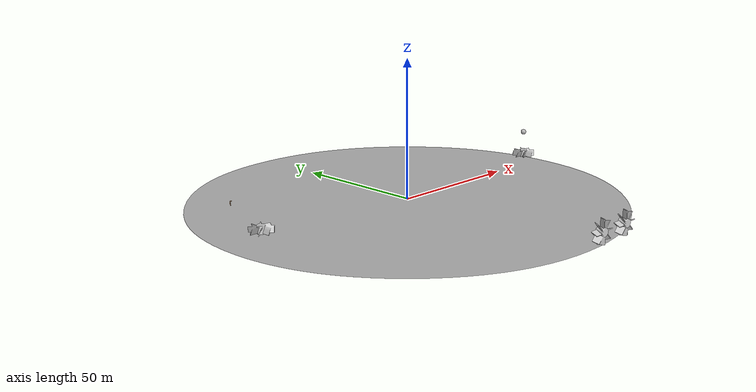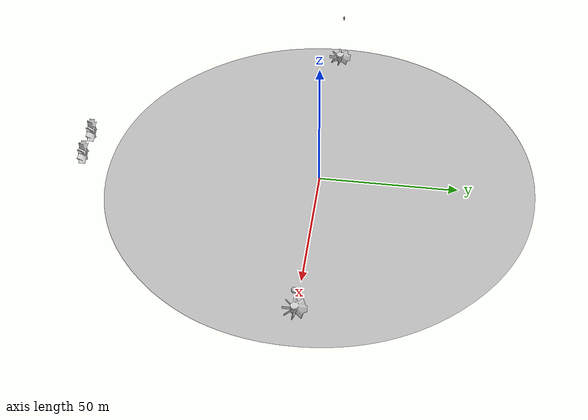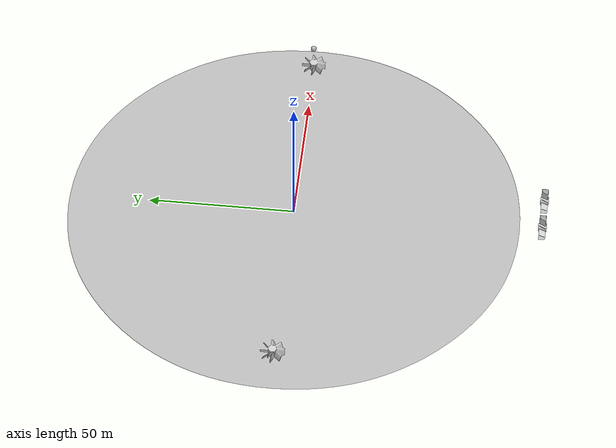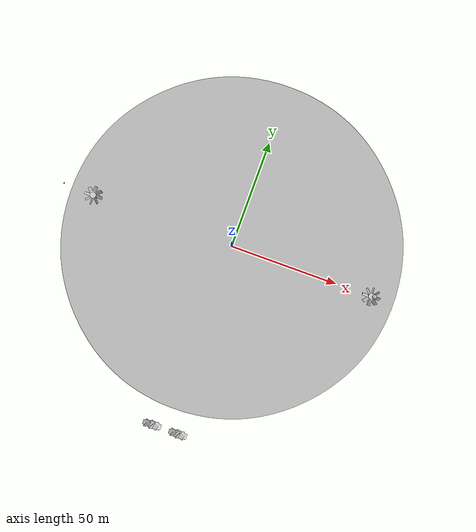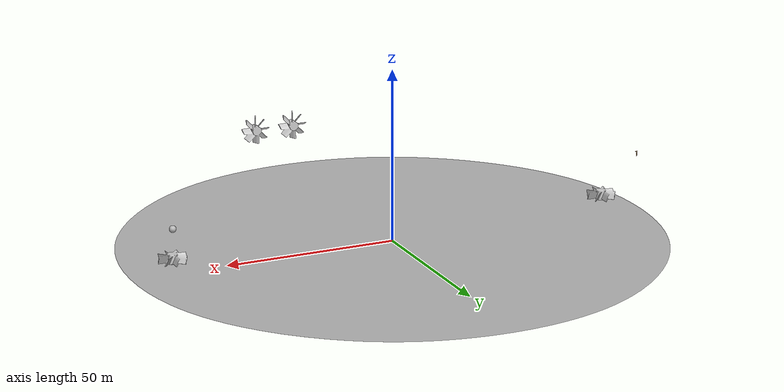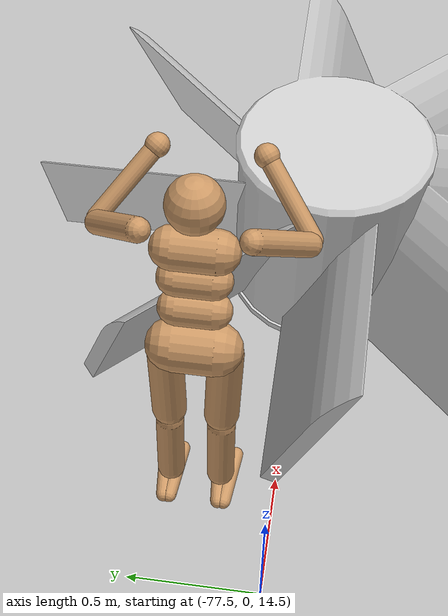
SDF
<sdf version="1.9">
 <world name="Garden">
  <gravity>0 0 -1.62</gravity>
  <scene><ambient>0.0 0.0 0.0 0.0</ambient><background>0.0 0.0 0.0 1.0</background><grid>false</grid></scene>
  <plugin filename="gz-sim-physics-system" name="gz::sim::systems::Physics"/>
  <plugin filename="gz-sim-sensors-system" name="gz::sim::systems::Sensors">
   <render_engine>ogre2</render_engine>
  </plugin>
  <plugin filename="gz-sim-user-commands-system" name="gz::sim::systems::UserCommands"/>
  <plugin filename="gz-sim-scene-broadcaster-system" name="gz::sim::systems::SceneBroadcaster"/>
  <light type="directional" name="sun">
   <pose>0 0 10 0 0 0</pose>
   <diffuse>0.8 0.8 0.8 1</diffuse>
   <specular>0.05 0.05 0.05 1</specular>
   <direction>-1 0.0 -0.4</direction>
   <visualize>false</visualize>
  </light>
  <light type="spot" name="dome_light">
   <cast_shadows>false</cast_shadows>
   <pose>0 0 50 0 0 0</pose>
   <diffuse>0.8 0.8 0.8 1</diffuse>
   <specular>0.8 0.8 0.8 1</specular>
   <attenuation>
    <range>110</range>
    <constant>0.0</constant>
    <linear>0.001</linear>
    <quadratic>0.0001</quadratic>
   </attenuation>
   <spot><inner_angle>2.9</inner_angle><outer_angle>3.1</outer_angle><falloff>0.0</falloff></spot>
   <direction>0 0.0 -1</direction>
   <visualize>false</visualize>
  </light>
  <light type="spot" name="dome_light_01">
   <cast_shadows>false</cast_shadows>
   <pose>0 45 30 0 0 0</pose>
   <diffuse>0.8 0.8 0.8 1</diffuse>
   <specular>0.8 0.8 0.8 1</specular>
   <attenuation>
    <range>70</range>
    <constant>0.2</constant>
    <linear>0.017</linear>
    <quadratic>0.0001</quadratic>
   </attenuation>
   <spot><inner_angle>2.0</inner_angle><outer_angle>2.5</outer_angle><falloff>0.6</falloff></spot>
   <direction>0 0.0 -1</direction>
   <visualize>false</visualize>
  </light>
  <light type="spot" name="dome_light_02">
   <cast_shadows>false</cast_shadows>
   <pose>0 -45 30 0 0 0</pose>
   <diffuse>0.8 0.8 0.8 1</diffuse>
   <specular>0.8 0.8 0.8 1</specular>
   <attenuation>
    <range>70</range>
    <constant>0.2</constant>
    <linear>0.017</linear>
    <quadratic>0.0001</quadratic>
   </attenuation>
   <spot><inner_angle>2.0</inner_angle><outer_angle>2.5</outer_angle><falloff>0.6</falloff></spot>
   <direction>0 0.0 -1</direction>
   <visualize>false</visualize>
  </light>
  <light type="spot" name="dome_light_03">
   <cast_shadows>false</cast_shadows>
   <pose>45 0 30 0 0 0</pose>
   <diffuse>0.8 0.8 0.8 1</diffuse>
   <specular>0.8 0.8 0.8 1</specular>
   <attenuation>
    <range>70</range>
    <constant>0.2</constant>
    <linear>0.017</linear>
    <quadratic>0.0001</quadratic>
   </attenuation>
   <spot><inner_angle>2.0</inner_angle><outer_angle>2.5</outer_angle><falloff>0.6</falloff></spot>
   <direction>0 0.0 -1</direction>
   <visualize>false</visualize>
  </light>
  <light type="spot" name="dome_light_04">
   <cast_shadows>false</cast_shadows>
   <pose>-45 0 30 0 0 0</pose>
   <diffuse>0.8 0.8 0.8 1</diffuse>
   <specular>0.8 0.8 0.8 1</specular>
   <attenuation>
    <range>70</range>
    <constant>0.2</constant>
    <linear>0.017</linear>
    <quadratic>0.0001</quadratic>
   </attenuation>
   <spot><inner_angle>2.0</inner_angle><outer_angle>2.5</outer_angle><falloff>0.6</falloff></spot>
   <direction>0 0.0 -1</direction>
   <visualize>false</visualize>
  </light>
  <light type="spot" name="tunnel_light_01">
   <cast_shadows>false</cast_shadows>
   <pose>0.2841 98.4191 10 0 0 0</pose>
   <diffuse>0.8 0.8 0.8 1</diffuse>
   <specular>0.8 0.8 0.8 1</specular>
   <attenuation>
    <range>10</range>
    <constant>0.2</constant>
    <linear>0.2517</linear>
    <quadratic>0.0001</quadratic>
   </attenuation>
   <spot><inner_angle>0.0</inner_angle><outer_angle>2.5</outer_angle><falloff>0.6</falloff></spot>
   <direction>0 0.0 -1</direction>
   <visualize>false</visualize>
  </light>
  <light type="spot" name="tunnel_light_02">
   <cast_shadows>false</cast_shadows>
   <pose>-0.0615 110.8810 7.8431 0 0 0</pose>
   <diffuse>0.8 0.8 0.8 1</diffuse>
   <specular>0.8 0.8 0.8 1</specular>
   <attenuation>
    <range>8</range>
    <constant>0.2</constant>
    <linear>0.2517</linear>
    <quadratic>0.0001</quadratic>
   </attenuation>
   <spot><inner_angle>0.0</inner_angle><outer_angle>2.5</outer_angle><falloff>0.6</falloff></spot>
   <direction>0 0.0 -1</direction>
   <visualize>false</visualize>
  </light>
  <include>
   <pose>0 0 -0.05 0 0 0</pose>
   <uri>https://fuel.gazebosim.org/1.0/OpenRobotics/models/Moon base water</uri>
  </include>
  <include>
   <name>Fan1</name>
   <pose>6.0 -85.217 8.88 0 0 0</pose>
   <uri>https://fuel.gazebosim.org/1.0/OpenRobotics/models/Moon base fan blade</uri>
   <params>
    <collision element_id="Fan::collision" action="remove"/>
    <plugin element_id="gz::sim::systems::JointController" action="modify">
     <initial_velocity>4.5</initial_velocity>
    </plugin>
   </params>
  </include>
  <include>
   <name>Fan2</name>
   <pose>-6 -85.217 8.88 0 0 0</pose>
   <uri>https://fuel.gazebosim.org/1.0/OpenRobotics/models/Moon base fan blade</uri>
   <params><collision element_id="Fan::collision" action="remove"/></params>
  </include>
  <include>
   <name>Fan3</name>
   <pose>65.9289 -0.0026 4.6064 1.5707963267948966 0 0</pose>
   <uri>https://fuel.gazebosim.org/1.0/OpenRobotics/models/Moon base fan blade</uri>
   <params>
    <collision element_id="Fan::collision" action="remove"/>
    <plugin element_id="gz::sim::systems::JointController" action="modify">
     <initial_velocity>9</initial_velocity>
    </plugin>
   </params>
  </include>
  <plugin filename="gz-sim-wind-effects-system" name="gz::sim::systems::WindEffects">
   <force_approximation_scaling_factor>
    <when zgt="8.0" zlt="60.0" xlt="69.865" xgt="61.535" ylt="4.165" ygt="-4.165">
     <k>0.9</k>
     <rz>0 0 -0.019 1.14</rz>
    </when>
    <when zgt="8.0" zlt="60.0" xlt="69.865" xgt="61.535" yle="-4.165">0</when>
    <when zgt="8.0" zlt="60.0" xlt="69.865" xgt="61.535" yge="4.165">0</when>
    <when zgt="8.0" zlt="60.0" xge="69.865">0</when>
    <when zgt="8.0" zlt="60.0" xle="4.165">0</when>
    <when zge="60.0">0</when>
    <when zle="8.0">0</when>
   </force_approximation_scaling_factor>
   <vertical><time_for_rise>1</time_for_rise><noise type="gaussian"><stddev>2</stddev></noise></vertical>
  </plugin>
  <wind><linear_velocity>0 0 2</linear_velocity></wind>
  <include>
   <name>Fan4</name>
   <pose>-65.9289 -0.0026 4.6064 1.5707963267948966 0 0</pose>
   <uri>https://fuel.gazebosim.org/1.0/OpenRobotics/models/Moon base fan blade</uri>
   <params><collision element_id="Fan::collision" action="remove"/></params>
  </include>
  <model name="Ball">
   <pose>65.7 0 13 0 0 0</pose>
   <link name="link">
    <enable_wind>1</enable_wind>
    <inertial>
     <mass>1</mass>
     <inertia>
      <ixx>0.666666</ixx>
      <ixy>0</ixy>
      <ixz>0</ixz>
      <iyy>0.666666</iyy>
      <iyz>0</iyz>
      <izz>0.666666</izz>
     </inertia>
    </inertial>
    <collision name="collision"><geometry><sphere><radius>1</radius></sphere></geometry></collision>
    <visual name="visual"><geometry><sphere><radius>1</radius></sphere></geometry></visual>
   </link>
  </model>
  <include>
   <pose>-77.1886 0.2825 14.4945 0 0 0</pose>
   <uri>https://fuel.gazebosim.org/1.0/OpenRobotics/models/Humanoid from MJCF</uri>
  </include>
 </world>
</sdf>

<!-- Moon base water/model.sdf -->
<sdf version="1.9">
  <model name="moon_base_water">
    <static>true</static>
    <link name="link">
      <visual name="visual">
        <pose>0 0 0 0 0 -1.570796</pose>
        <geometry>
          <mesh>
            <uri>meshes/MoonBaseWater.dae</uri>
          </mesh>
        </geometry>

        <plugin filename="gz-sim-shader-param-system" name="gz::sim::systems::ShaderParam">
          <shader language="glsl">
            <vertex>materials/programs/GerstnerWaves_vs_330.glsl</vertex>
            <fragment>materials/programs/GerstnerWaves_fs_330.glsl</fragment>
          </shader>
          <shader language="metal">
            <vertex>materials/programs/GerstnerWaves_vs.metal</vertex>
            <fragment>materials/programs/GerstnerWaves_fs.metal</fragment>
          </shader>
          <param>
            <shader>vertex</shader>
            <name>Nwaves</name>
            <type>int</type>
            <value>3</value>
          </param>
          <param>
            <shader>vertex</shader>
            <name>rescale</name>
            <type>float</type>
            <value>0.25</value>
          </param>
          <param>
            <shader>vertex</shader>
            <name>bumpScale</name>
            <type>float_array</type>
            <value>30 30</value>
          </param>
          <param>
            <shader>vertex</shader>
            <name>bumpSpeed</name>
            <type>float_array</type>
            <value>0.015 0.0</value>
          </param>
          <param>
            <shader>vertex</shader>
            <name>amplitude</name>
            <type>float_array</type>
            <value>0.01 0.02, 0.03</value>
          </param>
          <param>
            <shader>vertex</shader>
            <name>wavenumber</name>
            <type>float_array</type>
            <value>0.028 0.0896 0.0504</value>
          </param>
          <param>
            <shader>vertex</shader>
            <name>omega</name>
            <type>float_array</type>
            <value>0.5 1.7 1.0</value>
          </param>
          <param>
            <shader>vertex</shader>
            <name>dir0</name>
            <type>float_array</type>
            <value>1.0 0.0</value>
          </param>
          <param>
            <shader>vertex</shader>
            <name>dir1</name>
            <type>float_array</type>
            <value>0.7 0.3</value>
          </param>
          <param>
            <shader>vertex</shader>
            <name>dir2</name>
            <type>float_array</type>
            <value>0.7 -0.3</value>
          </param>
          <param>
            <shader>vertex</shader>
            <name>steepness</name>
            <type>float_array</type>
            <value>1.0 1.5 0.8</value>
          </param>
          <param>
            <shader>vertex</shader>
            <name>tau</name>
            <type>float</type>
            <value>2.0</value>
          </param>
          <param>
            <shader>vertex</shader>
            <name>camera_position_object_space</name>
          </param>
          <param>
            <shader>vertex</shader>
            <name>worldviewproj_matrix</name>
          </param>
          <param>
            <shader>vertex</shader>
            <name>t</name>
            <value>TIME</value>
          </param>
          <param>
            <shader>fragment</shader>
            <name>hdrMultiplier</name>
            <type>float</type>
            <value>0.4</value>
          </param>
          <param>
            <shader>fragment</shader>
            <name>fresnelPower</name>
            <type>float</type>
            <value>5.0</value>
          </param>
          <param>
            <shader>fragment</shader>
            <name>shallowColor</name>
            <type>float_array</type>
            <value>0.0 0.1 0.3 1.0</value>
          </param>
          <param>
            <shader>fragment</shader>
            <name>deepColor</name>
            <type>float_array</type>
            <value>0.0 0.05 0.02 1.0</value>
          </param>
          <param>
            <shader>fragment</shader>
            <name>cubeMap</name>
            <type>texture_cube</type>
            <value>materials/textures/skybox_lowres.dds</value>
            <!-- arg: texture coord set index -->
            <arg>1</arg>
          </param>
          <param>
            <shader>fragment</shader>
            <name>bumpMap</name>
            <type>texture</type>
            <value>materials/textures/wave_normals.dds</value>
          </param>
        </plugin>

      </visual>
    </link>

  </model>
</sdf>

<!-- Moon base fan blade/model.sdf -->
<sdf version="1.9">
  <model name="moon_base_fan_blade">
    <static>false</static>
    <link name="Fan">
      <collision name="collision">
        <pose>0 0 0 0 0 0</pose>
        <geometry>
          <mesh>
            <uri>meshes/Fan.dae</uri>
          </mesh>
        </geometry>
      </collision>
      <visual name="visual">
        <geometry>
          <mesh>
            <uri>meshes/Fan.dae</uri>
          </mesh>
        </geometry>
        <material>
          <ambient>0.8 0.8 0.8 1</ambient>
          <diffuse>0.8 0.8 0.8 1</diffuse>
          <specular>0.8 0.8 0.8 1</specular>
            <pbr>
              <metal>
                <albedo_map>materials/textures/Fan_Albedo.jpg</albedo_map>
                <normal_map>materials/textures/Fan_Normal.jpg</normal_map>
                <roughness_map>materials/textures/Fan_Roughness.jpg</roughness_map>
                <metalness_map>materials/textures/Fan_Metalness.jpg</metalness_map>
              </metal>
            </pbr>
        </material>

      </visual>
    </link>
    <joint name="fan_joint" type="revolute">
      <parent>world</parent>
      <child>Fan</child>
      <axis>
        <xyz>0 1 0</xyz>
      </axis>
    </joint>
    <plugin filename="gz-sim-joint-controller-system" name="gz::sim::systems::JointController">
      <joint_name>fan_joint</joint_name>
      <initial_velocity>4.0</initial_velocity>
    </plugin>
  </model>
</sdf>

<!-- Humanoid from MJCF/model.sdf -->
<sdf version="1.10">
  <model name='humanod_from_mjcf'>
    <static>false</static>
    <self_collide>false</self_collide>
    <allow_auto_disable>true</allow_auto_disable>
    <enable_wind>false</enable_wind>
    <pose>0 0 0 0 0 0</pose>
    <link name='torso'>
      <pose>0 0 1.5 0 0 0</pose>
      <inertial>
        <pose>-0.00386404 0 -0.0463685 0 0.083141200000000012 0</pose>
        <mass>5.8538300000000003</mass>
        <inertia>
          <ixx>0.051274199999999999</ixx>
          <ixy>0</ixy>
          <ixz>0</ixz>
          <iyy>0.031966700000000001</iyy>
          <iyz>0</iyz>
          <izz>0.031149300000000001</izz>
        </inertia>
      </inertial>
      <enable_wind>false</enable_wind>
      <collision name='collision_torso'>
        <pose>0 0 0 1.5708 0 0</pose>
        <geometry>
          <capsule>
            <radius>0.070000000000000007</radius>
            <length>0.14000000000000001</length>
          </capsule>
        </geometry>
        <surface>
          <contact>
            <collide_bitmask>255</collide_bitmask>
          </contact>
          <friction>
            <ode>
              <mu>0.69999999999999996</mu>
            </ode>
          </friction>
        </surface>
      </collision>
      <collision name='collision_upper_waist'>
        <pose>-0.01 0 -0.12 1.5708 0 0</pose>
        <geometry>
          <capsule>
            <radius>0.059999999999999998</radius>
            <length>0.12</length>
          </capsule>
        </geometry>
        <surface>
          <contact>
            <collide_bitmask>255</collide_bitmask>
          </contact>
          <friction>
            <ode>
              <mu>0.69999999999999996</mu>
            </ode>
          </friction>
        </surface>
      </collision>
      <light name='top' type='spot'>
        <pose>0 0 2 0 0 0</pose>
        <cast_shadows>false</cast_shadows>
        <intensity>1</intensity>
        <direction>0 0 -1</direction>
        <diffuse>0.699999988 0.699999988 0.699999988 1</diffuse>
        <specular>0.300000012 0.300000012 0.300000012 1</specular>
        <attenuation>
          <range>10</range>
          <linear>0</linear>
          <constant>1</constant>
          <quadratic>0</quadratic>
        </attenuation>
        <spot>
          <inner_angle>0</inner_angle>
          <outer_angle>1.5708</outer_angle>
          <falloff>2</falloff>
        </spot>
      </light>
      <sensor name='back' type='camera'>
        <pose>-3 0 1 7.8504600000000004e-17 7.8504600000000004e-17 -7.8504600000000004e-17</pose>
        <topic>__default__</topic>
        <update_rate>25</update_rate>
        <enable_metrics>false</enable_metrics>
        <camera>
          <pose>0 0 0 0 0 0</pose>
          <horizontal_fov>1.0469999999999999</horizontal_fov>
          <image>
            <width>320</width>
            <height>240</height>
            <format>RGB_INT8</format>
            <anti_aliasing>4</anti_aliasing>
          </image>
          <clip>
            <near>0.10000000000000001</near>
            <far>100</far>
          </clip>
          <save enabled='false'>
            <path>__default__</path>
          </save>
          <visibility_mask>4294967295</visibility_mask>
          <noise>
            <type>none</type>
            <mean>0</mean>
            <stddev>0</stddev>
          </noise>
          <distortion>
            <k1>0</k1>
            <k2>0</k2>
            <k3>0</k3>
            <p1>0</p1>
            <p2>0</p2>
            <center>0.5 0.5</center>
          </distortion>
          <lens>
            <type>stereographic</type>
            <scale_to_hfov>true</scale_to_hfov>
            <cutoff_angle>1.5708</cutoff_angle>
            <env_texture_size>256</env_texture_size>
          </lens>
        </camera>
      </sensor>
      <sensor name='side' type='camera'>
        <pose>0 -3 1 2.2204499999999999e-16 2.4651903288156619e-32 1.5708</pose>
        <topic>__default__</topic>
        <update_rate>25</update_rate>
        <enable_metrics>false</enable_metrics>
        <camera>
          <pose>0 0 0 0 0 0</pose>
          <horizontal_fov>1.0469999999999999</horizontal_fov>
          <image>
            <width>320</width>
            <height>240</height>
            <format>RGB_INT8</format>
            <anti_aliasing>4</anti_aliasing>
          </image>
          <clip>
            <near>0.10000000000000001</near>
            <far>100</far>
          </clip>
          <save enabled='false'>
            <path>__default__</path>
          </save>
          <visibility_mask>4294967295</visibility_mask>
          <noise>
            <type>none</type>
            <mean>0</mean>
            <stddev>0</stddev>
          </noise>
          <distortion>
            <k1>0</k1>
            <k2>0</k2>
            <k3>0</k3>
            <p1>0</p1>
            <p2>0</p2>
            <center>0.5 0.5</center>
          </distortion>
          <lens>
            <type>stereographic</type>
            <scale_to_hfov>true</scale_to_hfov>
            <cutoff_angle>1.5708</cutoff_angle>
            <env_texture_size>256</env_texture_size>
          </lens>
        </camera>
      </sensor>
      <visual name='visual_torso'>
        <pose>0 0 0 1.5708 0 0</pose>
        <geometry>
          <capsule>
            <radius>0.070000000000000007</radius>
            <length>0.14000000000000001</length>
          </capsule>
        </geometry>
        <cast_shadows>true</cast_shadows>
        <laser_retro>0</laser_retro>
        <transparency>0</transparency>
        <visibility_flags>4294967295</visibility_flags>
        <material>
          <ambient>0.800000012 0.600000024 0.400000006 1</ambient>
          <diffuse>0.800000012 0.600000024 0.400000006 1</diffuse>
          <specular>0.5 0.5 0.5 1</specular>
          <emissive>0 0 0 1</emissive>
          <render_order>0</render_order>
          <lighting>true</lighting>
          <double_sided>false</double_sided>
          <shader type='pixel'/>
        </material>
      </visual>
      <visual name='visual_upper_waist'>
        <pose>-0.01 0 -0.12 1.5708 0 0</pose>
        <geometry>
          <capsule>
            <radius>0.059999999999999998</radius>
            <length>0.12</length>
          </capsule>
        </geometry>
        <cast_shadows>true</cast_shadows>
        <laser_retro>0</laser_retro>
        <transparency>0</transparency>
        <visibility_flags>4294967295</visibility_flags>
        <material>
          <ambient>0.800000012 0.600000024 0.400000006 1</ambient>
          <diffuse>0.800000012 0.600000024 0.400000006 1</diffuse>
          <specular>0.5 0.5 0.5 1</specular>
          <emissive>0 0 0 1</emissive>
          <render_order>0</render_order>
          <lighting>true</lighting>
          <double_sided>false</double_sided>
          <shader type='pixel'/>
        </material>
      </visual>
    </link>
    <link name='head'>
      <pose relative_to='torso'>0 0 0.19 0 0 0</pose>
      <inertial>
        <pose>0 0 0 0 0 0</pose>
        <mass>3.0536300000000001</mass>
        <inertia>
          <ixx>0.0098937499999999998</ixx>
          <ixy>0</ixy>
          <ixz>0</ixz>
          <iyy>0.0098937499999999998</iyy>
          <iyz>0</iyz>
          <izz>0.0098937499999999998</izz>
        </inertia>
      </inertial>
      <enable_wind>false</enable_wind>
      <collision name='collision_head'>
        <pose>0 0 0 0 0 0</pose>
        <geometry>
          <sphere>
            <radius>0.089999999999999997</radius>
          </sphere>
        </geometry>
        <surface>
          <contact>
            <collide_bitmask>255</collide_bitmask>
          </contact>
          <friction>
            <ode>
              <mu>0.69999999999999996</mu>
            </ode>
          </friction>
        </surface>
      </collision>
      <sensor name='egocentric' type='camera'>
        <pose>0.089999999999999997 0 0 2.0641799999999998e-16 0.095166200000000006 -3.2285999999999994e-16</pose>
        <topic>__default__</topic>
        <update_rate>25</update_rate>
        <enable_metrics>false</enable_metrics>
        <camera>
          <pose>0 0 0 0 0 0</pose>
          <horizontal_fov>1.0469999999999999</horizontal_fov>
          <image>
            <width>320</width>
            <height>240</height>
            <format>RGB_INT8</format>
            <anti_aliasing>4</anti_aliasing>
          </image>
          <clip>
            <near>0.10000000000000001</near>
            <far>100</far>
          </clip>
          <save enabled='false'>
            <path>__default__</path>
          </save>
          <visibility_mask>4294967295</visibility_mask>
          <noise>
            <type>none</type>
            <mean>0</mean>
            <stddev>0</stddev>
          </noise>
          <distortion>
            <k1>0</k1>
            <k2>0</k2>
            <k3>0</k3>
            <p1>0</p1>
            <p2>0</p2>
            <center>0.5 0.5</center>
          </distortion>
          <lens>
            <type>stereographic</type>
            <scale_to_hfov>true</scale_to_hfov>
            <cutoff_angle>1.5708</cutoff_angle>
            <env_texture_size>256</env_texture_size>
          </lens>
        </camera>
      </sensor>
      <visual name='visual_head'>
        <pose>0 0 0 0 0 0</pose>
        <geometry>
          <sphere>
            <radius>0.089999999999999997</radius>
          </sphere>
        </geometry>
        <cast_shadows>true</cast_shadows>
        <laser_retro>0</laser_retro>
        <transparency>0</transparency>
        <visibility_flags>4294967295</visibility_flags>
        <material>
          <ambient>0.800000012 0.600000024 0.400000006 1</ambient>
          <diffuse>0.800000012 0.600000024 0.400000006 1</diffuse>
          <specular>0.5 0.5 0.5 1</specular>
          <emissive>0 0 0 1</emissive>
          <render_order>0</render_order>
          <lighting>true</lighting>
          <double_sided>false</double_sided>
          <shader type='pixel'/>
        </material>
      </visual>
    </link>
    <link name='lower_waist'>
      <pose relative_to='torso'>-0.01 0 -0.26000000000000001 0 0 0</pose>
      <inertial>
        <pose>0 0 0 1.5708 0 0</pose>
        <mass>2.2619500000000001</mass>
        <inertia>
          <ixx>0.0098530400000000004</ixx>
          <ixy>0</ixy>
          <ixz>0</ixz>
          <iyy>0.0098530400000000004</iyy>
          <iyz>0</iyz>
          <izz>0.0037457800000000002</izz>
        </inertia>
      </inertial>
      <enable_wind>false</enable_wind>
      <collision name='collision_lower_waist'>
        <pose>0 0 0 1.5708 0 0</pose>
        <geometry>
          <capsule>
            <radius>0.059999999999999998</radius>
            <length>0.12</length>
          </capsule>
        </geometry>
        <surface>
          <contact>
            <collide_bitmask>255</collide_bitmask>
          </contact>
          <friction>
            <ode>
              <mu>0.69999999999999996</mu>
            </ode>
          </friction>
        </surface>
      </collision>
      <visual name='visual_lower_waist'>
        <pose>0 0 0 1.5708 0 0</pose>
        <geometry>
          <capsule>
            <radius>0.059999999999999998</radius>
            <length>0.12</length>
          </capsule>
        </geometry>
        <cast_shadows>true</cast_shadows>
        <laser_retro>0</laser_retro>
        <transparency>0</transparency>
        <visibility_flags>4294967295</visibility_flags>
        <material>
          <ambient>0.800000012 0.600000024 0.400000006 1</ambient>
          <diffuse>0.800000012 0.600000024 0.400000006 1</diffuse>
          <specular>0.5 0.5 0.5 1</specular>
          <emissive>0 0 0 1</emissive>
          <render_order>0</render_order>
          <lighting>true</lighting>
          <double_sided>false</double_sided>
          <shader type='pixel'/>
        </material>
      </visual>
    </link>
    <link name='lower_waist_dummy_0'>
      <pose relative_to='lower_waist'>0 0 0 0 0 0</pose>
      <inertial>
        <pose>0 0 0 0 0 0</pose>
        <mass>9.9999999999999995e-07</mass>
        <inertia>
          <ixx>3.9999999999999998e-07</ixx>
          <ixy>0</ixy>
          <ixz>0</ixz>
          <iyy>3.9999999999999998e-07</iyy>
          <iyz>0</iyz>
          <izz>3.9999999999999998e-07</izz>
        </inertia>
      </inertial>
      <enable_wind>false</enable_wind>
    </link>
    <link name='pelvis'>
      <pose relative_to='lower_waist'>0 0 -0.16500000000000001 0 0 0</pose>
      <inertial>
        <pose>-0.02 0 0 1.5708 0 0</pose>
        <mass>6.6161899999999996</mass>
        <inertia>
          <ixx>0.052318000000000003</ixx>
          <ixy>0</ixy>
          <ixz>0</ixz>
          <iyy>0.052318000000000003</iyy>
          <iyz>0</iyz>
          <izz>0.024322099999999999</izz>
        </inertia>
      </inertial>
      <enable_wind>false</enable_wind>
      <collision name='collision_butt'>
        <pose>-0.02 0 0 1.5708 0 0</pose>
        <geometry>
          <capsule>
            <radius>0.089999999999999997</radius>
            <length>0.14000000000000001</length>
          </capsule>
        </geometry>
        <surface>
          <contact>
            <collide_bitmask>255</collide_bitmask>
          </contact>
          <friction>
            <ode>
              <mu>0.69999999999999996</mu>
            </ode>
          </friction>
        </surface>
      </collision>
      <visual name='visual_butt'>
        <pose>-0.02 0 0 1.5708 0 0</pose>
        <geometry>
          <capsule>
            <radius>0.089999999999999997</radius>
            <length>0.14000000000000001</length>
          </capsule>
        </geometry>
        <cast_shadows>true</cast_shadows>
        <laser_retro>0</laser_retro>
        <transparency>0</transparency>
        <visibility_flags>4294967295</visibility_flags>
        <material>
          <ambient>0.800000012 0.600000024 0.400000006 1</ambient>
          <diffuse>0.800000012 0.600000024 0.400000006 1</diffuse>
          <specular>0.5 0.5 0.5 1</specular>
          <emissive>0 0 0 1</emissive>
          <render_order>0</render_order>
          <lighting>true</lighting>
          <double_sided>false</double_sided>
          <shader type='pixel'/>
        </material>
      </visual>
    </link>
    <link name='right_thigh'>
      <pose relative_to='pelvis'>0 -0.10000000000000001 -0.040000000000000001 0 0 0</pose>
      <inertial>
        <pose>0 0.0050000000000000001 -0.17000000000000001 0.029403299999999997 0 0</pose>
        <mass>4.7517500000000004</mass>
        <inertia>
          <ixx>0.074951699999999996</ixx>
          <ixy>0</ixy>
          <ixz>0</ixz>
          <iyy>0.074951699999999996</iyy>
          <iyz>0</iyz>
          <izz>0.0082274300000000009</izz>
        </inertia>
      </inertial>
      <enable_wind>false</enable_wind>
      <collision name='collision_right_thigh'>
        <pose>0 0.0050000000000000001 -0.17000000000000001 0.029403299999999997 0 0</pose>
        <geometry>
          <capsule>
            <radius>0.059999999999999998</radius>
            <length>0.34014699999999998</length>
          </capsule>
        </geometry>
        <surface>
          <contact>
            <collide_bitmask>255</collide_bitmask>
          </contact>
          <friction>
            <ode>
              <mu>0.69999999999999996</mu>
            </ode>
          </friction>
        </surface>
      </collision>
      <visual name='visual_right_thigh'>
        <pose>0 0.0050000000000000001 -0.17000000000000001 0.029403299999999997 0 0</pose>
        <geometry>
          <capsule>
            <radius>0.059999999999999998</radius>
            <length>0.34014699999999998</length>
          </capsule>
        </geometry>
        <cast_shadows>true</cast_shadows>
        <laser_retro>0</laser_retro>
        <transparency>0</transparency>
        <visibility_flags>4294967295</visibility_flags>
        <material>
          <ambient>0.800000012 0.600000024 0.400000006 1</ambient>
          <diffuse>0.800000012 0.600000024 0.400000006 1</diffuse>
          <specular>0.5 0.5 0.5 1</specular>
          <emissive>0 0 0 1</emissive>
          <render_order>0</render_order>
          <lighting>true</lighting>
          <double_sided>false</double_sided>
          <shader type='pixel'/>
        </material>
      </visual>
    </link>
    <link name='right_thigh_dummy_0'>
      <pose relative_to='right_thigh'>0 0 0 0 0 0</pose>
      <inertial>
        <pose>0 0 0 0 0 0</pose>
        <mass>9.9999999999999995e-07</mass>
        <inertia>
          <ixx>3.9999999999999998e-07</ixx>
          <ixy>0</ixy>
          <ixz>0</ixz>
          <iyy>3.9999999999999998e-07</iyy>
          <iyz>0</iyz>
          <izz>3.9999999999999998e-07</izz>
        </inertia>
      </inertial>
      <enable_wind>false</enable_wind>
    </link>
    <link name='right_thigh_dummy_1'>
      <pose relative_to='right_thigh'>0 0 0 0 0 0</pose>
      <inertial>
        <pose>0 0 0 0 0 0</pose>
        <mass>9.9999999999999995e-07</mass>
        <inertia>
          <ixx>3.9999999999999998e-07</ixx>
          <ixy>0</ixy>
          <ixz>0</ixz>
          <iyy>3.9999999999999998e-07</iyy>
          <iyz>0</iyz>
          <izz>3.9999999999999998e-07</izz>
        </inertia>
      </inertial>
      <enable_wind>false</enable_wind>
    </link>
    <link name='right_shin'>
      <pose relative_to='right_thigh'>0 0.01 -0.40300000000000002 0 0 0</pose>
      <inertial>
        <pose>0 0 -0.14999999999999999 0 0 0</pose>
        <mass>2.7557</mass>
        <inertia>
          <ixx>0.032607999999999998</ixx>
          <ixy>0</ixy>
          <ixz>0</ixz>
          <iyy>0.032607999999999998</iyy>
          <iyz>0</iyz>
          <izz>0.0031898899999999999</izz>
        </inertia>
      </inertial>
      <enable_wind>false</enable_wind>
      <collision name='collision_right_shin'>
        <pose>0 0 -0.14999999999999999 0 0 0</pose>
        <geometry>
          <capsule>
            <radius>0.049000000000000002</radius>
            <length>0.29999999999999999</length>
          </capsule>
        </geometry>
        <surface>
          <contact>
            <collide_bitmask>255</collide_bitmask>
          </contact>
          <friction>
            <ode>
              <mu>0.69999999999999996</mu>
            </ode>
          </friction>
        </surface>
      </collision>
      <visual name='visual_right_shin'>
        <pose>0 0 -0.14999999999999999 0 0 0</pose>
        <geometry>
          <capsule>
            <radius>0.049000000000000002</radius>
            <length>0.29999999999999999</length>
          </capsule>
        </geometry>
        <cast_shadows>true</cast_shadows>
        <laser_retro>0</laser_retro>
        <transparency>0</transparency>
        <visibility_flags>4294967295</visibility_flags>
        <material>
          <ambient>0.800000012 0.600000024 0.400000006 1</ambient>
          <diffuse>0.800000012 0.600000024 0.400000006 1</diffuse>
          <specular>0.5 0.5 0.5 1</specular>
          <emissive>0 0 0 1</emissive>
          <render_order>0</render_order>
          <lighting>true</lighting>
          <double_sided>false</double_sided>
          <shader type='pixel'/>
        </material>
      </visual>
    </link>
    <link name='right_foot'>
      <pose relative_to='right_shin'>0 0 -0.39000000000000001 0 0 0</pose>
      <inertial>
        <pose>0.035000000000000003 -0.01 0 2.6535897933410511e-06 -1.5707926536359933 3.1415926535897931</pose>
        <mass>1.13114</mass>
        <inertia>
          <ixx>0.0064464600000000002</ixx>
          <ixy>0</ixy>
          <ixz>0</ixz>
          <iyy>0.0059437200000000004</iyy>
          <iyz>0</iyz>
          <izz>0.00090301699999999999</izz>
        </inertia>
      </inertial>
      <enable_wind>false</enable_wind>
      <collision name='collision_right_right_foot'>
        <pose>0.035000000000000003 -0.029999999999999999 0 -1.5708000000000009 -1.47584 1.4758400000000012</pose>
        <geometry>
          <capsule>
            <radius>0.027</radius>
            <length>0.21095</length>
          </capsule>
        </geometry>
        <surface>
          <contact>
            <collide_bitmask>255</collide_bitmask>
          </contact>
          <friction>
            <ode>
              <mu>0.69999999999999996</mu>
            </ode>
          </friction>
        </surface>
      </collision>
      <collision name='collision_left_right_foot'>
        <pose>0.035000000000000003 0.01 0 1.5708000000000009 -1.47584 -1.4758400000000012</pose>
        <geometry>
          <capsule>
            <radius>0.027</radius>
            <length>0.21095</length>
          </capsule>
        </geometry>
        <surface>
          <contact>
            <collide_bitmask>255</collide_bitmask>
          </contact>
          <friction>
            <ode>
              <mu>0.69999999999999996</mu>
            </ode>
          </friction>
        </surface>
      </collision>
      <visual name='visual_right_right_foot'>
        <pose>0.035000000000000003 -0.029999999999999999 0 -1.5708000000000009 -1.47584 1.4758400000000012</pose>
        <geometry>
          <capsule>
            <radius>0.027</radius>
            <length>0.21095</length>
          </capsule>
        </geometry>
        <cast_shadows>true</cast_shadows>
        <laser_retro>0</laser_retro>
        <transparency>0</transparency>
        <visibility_flags>4294967295</visibility_flags>
        <material>
          <ambient>0.800000012 0.600000024 0.400000006 1</ambient>
          <diffuse>0.800000012 0.600000024 0.400000006 1</diffuse>
          <specular>0.5 0.5 0.5 1</specular>
          <emissive>0 0 0 1</emissive>
          <render_order>0</render_order>
          <lighting>true</lighting>
          <double_sided>false</double_sided>
          <shader type='pixel'/>
        </material>
      </visual>
      <visual name='visual_left_right_foot'>
        <pose>0.035000000000000003 0.01 0 1.5708000000000009 -1.47584 -1.4758400000000012</pose>
        <geometry>
          <capsule>
            <radius>0.027</radius>
            <length>0.21095</length>
          </capsule>
        </geometry>
        <cast_shadows>true</cast_shadows>
        <laser_retro>0</laser_retro>
        <transparency>0</transparency>
        <visibility_flags>4294967295</visibility_flags>
        <material>
          <ambient>0.800000012 0.600000024 0.400000006 1</ambient>
          <diffuse>0.800000012 0.600000024 0.400000006 1</diffuse>
          <specular>0.5 0.5 0.5 1</specular>
          <emissive>0 0 0 1</emissive>
          <render_order>0</render_order>
          <lighting>true</lighting>
          <double_sided>false</double_sided>
          <shader type='pixel'/>
        </material>
      </visual>
    </link>
    <link name='right_foot_dummy_0'>
      <pose relative_to='right_foot'>0 0 0 0 0 0</pose>
      <inertial>
        <pose>0 0 0 0 0 0</pose>
        <mass>9.9999999999999995e-07</mass>
        <inertia>
          <ixx>3.9999999999999998e-07</ixx>
          <ixy>0</ixy>
          <ixz>0</ixz>
          <iyy>3.9999999999999998e-07</iyy>
          <iyz>0</iyz>
          <izz>3.9999999999999998e-07</izz>
        </inertia>
      </inertial>
      <enable_wind>false</enable_wind>
    </link>
    <link name='left_thigh'>
      <pose relative_to='pelvis'>0 0.10000000000000001 -0.040000000000000001 0 0 0</pose>
      <inertial>
        <pose>0 -0.0050000000000000001 -0.17000000000000001 -0.029403299999999997 0 0</pose>
        <mass>4.7517500000000004</mass>
        <inertia>
          <ixx>0.074951699999999996</ixx>
          <ixy>0</ixy>
          <ixz>0</ixz>
          <iyy>0.074951699999999996</iyy>
          <iyz>0</iyz>
          <izz>0.0082274300000000009</izz>
        </inertia>
      </inertial>
      <enable_wind>false</enable_wind>
      <collision name='collision_left_thigh'>
        <pose>0 -0.0050000000000000001 -0.17000000000000001 -0.029403299999999997 0 0</pose>
        <geometry>
          <capsule>
            <radius>0.059999999999999998</radius>
            <length>0.34014699999999998</length>
          </capsule>
        </geometry>
        <surface>
          <contact>
            <collide_bitmask>255</collide_bitmask>
          </contact>
          <friction>
            <ode>
              <mu>0.69999999999999996</mu>
            </ode>
          </friction>
        </surface>
      </collision>
      <visual name='visual_left_thigh'>
        <pose>0 -0.0050000000000000001 -0.17000000000000001 -0.029403299999999997 0 0</pose>
        <geometry>
          <capsule>
            <radius>0.059999999999999998</radius>
            <length>0.34014699999999998</length>
          </capsule>
        </geometry>
        <cast_shadows>true</cast_shadows>
        <laser_retro>0</laser_retro>
        <transparency>0</transparency>
        <visibility_flags>4294967295</visibility_flags>
        <material>
          <ambient>0.800000012 0.600000024 0.400000006 1</ambient>
          <diffuse>0.800000012 0.600000024 0.400000006 1</diffuse>
          <specular>0.5 0.5 0.5 1</specular>
          <emissive>0 0 0 1</emissive>
          <render_order>0</render_order>
          <lighting>true</lighting>
          <double_sided>false</double_sided>
          <shader type='pixel'/>
        </material>
      </visual>
    </link>
    <link name='left_thigh_dummy_0'>
      <pose relative_to='left_thigh'>0 0 0 0 0 0</pose>
      <inertial>
        <pose>0 0 0 0 0 0</pose>
        <mass>9.9999999999999995e-07</mass>
        <inertia>
          <ixx>3.9999999999999998e-07</ixx>
          <ixy>0</ixy>
          <ixz>0</ixz>
          <iyy>3.9999999999999998e-07</iyy>
          <iyz>0</iyz>
          <izz>3.9999999999999998e-07</izz>
        </inertia>
      </inertial>
      <enable_wind>false</enable_wind>
    </link>
    <link name='left_thigh_dummy_1'>
      <pose relative_to='left_thigh'>0 0 0 0 0 0</pose>
      <inertial>
        <pose>0 0 0 0 0 0</pose>
        <mass>9.9999999999999995e-07</mass>
        <inertia>
          <ixx>3.9999999999999998e-07</ixx>
          <ixy>0</ixy>
          <ixz>0</ixz>
          <iyy>3.9999999999999998e-07</iyy>
          <iyz>0</iyz>
          <izz>3.9999999999999998e-07</izz>
        </inertia>
      </inertial>
      <enable_wind>false</enable_wind>
    </link>
    <link name='left_shin'>
      <pose relative_to='left_thigh'>0 -0.01 -0.40300000000000002 0 0 0</pose>
      <inertial>
        <pose>0 0 -0.14999999999999999 0 0 0</pose>
        <mass>2.7557</mass>
        <inertia>
          <ixx>0.032607999999999998</ixx>
          <ixy>0</ixy>
          <ixz>0</ixz>
          <iyy>0.032607999999999998</iyy>
          <iyz>0</iyz>
          <izz>0.0031898899999999999</izz>
        </inertia>
      </inertial>
      <enable_wind>false</enable_wind>
      <collision name='collision_left_shin'>
        <pose>0 0 -0.14999999999999999 0 0 0</pose>
        <geometry>
          <capsule>
            <radius>0.049000000000000002</radius>
            <length>0.29999999999999999</length>
          </capsule>
        </geometry>
        <surface>
          <contact>
            <collide_bitmask>255</collide_bitmask>
          </contact>
          <friction>
            <ode>
              <mu>0.69999999999999996</mu>
            </ode>
          </friction>
        </surface>
      </collision>
      <visual name='visual_left_shin'>
        <pose>0 0 -0.14999999999999999 0 0 0</pose>
        <geometry>
          <capsule>
            <radius>0.049000000000000002</radius>
            <length>0.29999999999999999</length>
          </capsule>
        </geometry>
        <cast_shadows>true</cast_shadows>
        <laser_retro>0</laser_retro>
        <transparency>0</transparency>
        <visibility_flags>4294967295</visibility_flags>
        <material>
          <ambient>0.800000012 0.600000024 0.400000006 1</ambient>
          <diffuse>0.800000012 0.600000024 0.400000006 1</diffuse>
          <specular>0.5 0.5 0.5 1</specular>
          <emissive>0 0 0 1</emissive>
          <render_order>0</render_order>
          <lighting>true</lighting>
          <double_sided>false</double_sided>
          <shader type='pixel'/>
        </material>
      </visual>
    </link>
    <link name='left_foot'>
      <pose relative_to='left_shin'>0 0 -0.39000000000000001 0 0 0</pose>
      <inertial>
        <pose>0.035000000000000003 0.01 0 2.6535897933410511e-06 -1.5707926536359933 3.1415926535897931</pose>
        <mass>1.13114</mass>
        <inertia>
          <ixx>0.0064464600000000002</ixx>
          <ixy>0</ixy>
          <ixz>0</ixz>
          <iyy>0.0059437200000000004</iyy>
          <iyz>0</iyz>
          <izz>0.00090301699999999999</izz>
        </inertia>
      </inertial>
      <enable_wind>false</enable_wind>
      <collision name='collision_left_left_foot'>
        <pose>0.035000000000000003 0.029999999999999999 0 1.5708000000000009 -1.47584 -1.4758400000000012</pose>
        <geometry>
          <capsule>
            <radius>0.027</radius>
            <length>0.21095</length>
          </capsule>
        </geometry>
        <surface>
          <contact>
            <collide_bitmask>255</collide_bitmask>
          </contact>
          <friction>
            <ode>
              <mu>0.69999999999999996</mu>
            </ode>
          </friction>
        </surface>
      </collision>
      <collision name='collision_right_left_foot'>
        <pose>0.035000000000000003 -0.01 0 -1.5708000000000009 -1.47584 1.4758400000000012</pose>
        <geometry>
          <capsule>
            <radius>0.027</radius>
            <length>0.21095</length>
          </capsule>
        </geometry>
        <surface>
          <contact>
            <collide_bitmask>255</collide_bitmask>
          </contact>
          <friction>
            <ode>
              <mu>0.69999999999999996</mu>
            </ode>
          </friction>
        </surface>
      </collision>
      <visual name='visual_left_left_foot'>
        <pose>0.035000000000000003 0.029999999999999999 0 1.5708000000000009 -1.47584 -1.4758400000000012</pose>
        <geometry>
          <capsule>
            <radius>0.027</radius>
            <length>0.21095</length>
          </capsule>
        </geometry>
        <cast_shadows>true</cast_shadows>
        <laser_retro>0</laser_retro>
        <transparency>0</transparency>
        <visibility_flags>4294967295</visibility_flags>
        <material>
          <ambient>0.800000012 0.600000024 0.400000006 1</ambient>
          <diffuse>0.800000012 0.600000024 0.400000006 1</diffuse>
          <specular>0.5 0.5 0.5 1</specular>
          <emissive>0 0 0 1</emissive>
          <render_order>0</render_order>
          <lighting>true</lighting>
          <double_sided>false</double_sided>
          <shader type='pixel'/>
        </material>
      </visual>
      <visual name='visual_right_left_foot'>
        <pose>0.035000000000000003 -0.01 0 -1.5708000000000009 -1.47584 1.4758400000000012</pose>
        <geometry>
          <capsule>
            <radius>0.027</radius>
            <length>0.21095</length>
          </capsule>
        </geometry>
        <cast_shadows>true</cast_shadows>
        <laser_retro>0</laser_retro>
        <transparency>0</transparency>
        <visibility_flags>4294967295</visibility_flags>
        <material>
          <ambient>0.800000012 0.600000024 0.400000006 1</ambient>
          <diffuse>0.800000012 0.600000024 0.400000006 1</diffuse>
          <specular>0.5 0.5 0.5 1</specular>
          <emissive>0 0 0 1</emissive>
          <render_order>0</render_order>
          <lighting>true</lighting>
          <double_sided>false</double_sided>
          <shader type='pixel'/>
        </material>
      </visual>
    </link>
    <link name='left_foot_dummy_0'>
      <pose relative_to='left_foot'>0 0 0 0 0 0</pose>
      <inertial>
        <pose>0 0 0 0 0 0</pose>
        <mass>9.9999999999999995e-07</mass>
        <inertia>
          <ixx>3.9999999999999998e-07</ixx>
          <ixy>0</ixy>
          <ixz>0</ixz>
          <iyy>3.9999999999999998e-07</iyy>
          <iyz>0</iyz>
          <izz>3.9999999999999998e-07</izz>
        </inertia>
      </inertial>
      <enable_wind>false</enable_wind>
    </link>
    <link name='right_upper_arm'>
      <pose relative_to='torso'>0 -0.17000000000000001 0.059999999999999998 0 0 0</pose>
      <inertial>
        <pose>0.080000000000000002 -0.080000000000000002 -0.080000000000000002 -0.78539800000000026 -0.61548000000000003 0.26179900000000006</pose>
        <mass>1.6610799999999999</mass>
        <inertia>
          <ixx>0.015905499999999999</ixx>
          <ixy>0</ixy>
          <ixz>0</ixz>
          <iyy>0.015905499999999999</iyy>
          <iyz>0</iyz>
          <izz>0.00128597</izz>
        </inertia>
      </inertial>
      <enable_wind>false</enable_wind>
      <collision name='collision_right_upper_arm'>
        <pose>0.080000000000000002 -0.080000000000000002 -0.080000000000000002 -0.78539800000000026 -0.61548000000000003 0.26179900000000006</pose>
        <geometry>
          <capsule>
            <radius>0.040000000000000001</radius>
            <length>0.27712799999999999</length>
          </capsule>
        </geometry>
        <surface>
          <contact>
            <collide_bitmask>255</collide_bitmask>
          </contact>
          <friction>
            <ode>
              <mu>0.69999999999999996</mu>
            </ode>
          </friction>
        </surface>
      </collision>
      <visual name='visual_right_upper_arm'>
        <pose>0.080000000000000002 -0.080000000000000002 -0.080000000000000002 -0.78539800000000026 -0.61548000000000003 0.26179900000000006</pose>
        <geometry>
          <capsule>
            <radius>0.040000000000000001</radius>
            <length>0.27712799999999999</length>
          </capsule>
        </geometry>
        <cast_shadows>true</cast_shadows>
        <laser_retro>0</laser_retro>
        <transparency>0</transparency>
        <visibility_flags>4294967295</visibility_flags>
        <material>
          <ambient>0.800000012 0.600000024 0.400000006 1</ambient>
          <diffuse>0.800000012 0.600000024 0.400000006 1</diffuse>
          <specular>0.5 0.5 0.5 1</specular>
          <emissive>0 0 0 1</emissive>
          <render_order>0</render_order>
          <lighting>true</lighting>
          <double_sided>false</double_sided>
          <shader type='pixel'/>
        </material>
      </visual>
    </link>
    <link name='right_upper_arm_dummy_0'>
      <pose relative_to='right_upper_arm'>0 0 0 0 0 0</pose>
      <inertial>
        <pose>0 0 0 0 0 0</pose>
        <mass>9.9999999999999995e-07</mass>
        <inertia>
          <ixx>3.9999999999999998e-07</ixx>
          <ixy>0</ixy>
          <ixz>0</ixz>
          <iyy>3.9999999999999998e-07</iyy>
          <iyz>0</iyz>
          <izz>3.9999999999999998e-07</izz>
        </inertia>
      </inertial>
      <enable_wind>false</enable_wind>
    </link>
    <link name='right_lower_arm'>
      <pose relative_to='right_upper_arm'>0.17999999999999999 -0.17999999999999999 -0.17999999999999999 0 0 0</pose>
      <inertial>
        <pose>0.089999999999999997 0.089999999999999997 0.089999999999999997 2.3561899999999998 -0.61548000000000003 -1.3089999999999999</pose>
        <mass>0.96145800000000003</mass>
        <inertia>
          <ixx>0.0084016200000000003</ixx>
          <ixy>0</ixy>
          <ixz>0</ixz>
          <iyy>0.0084016200000000003</iyy>
          <iyz>0</iyz>
          <izz>0.00044998800000000002</izz>
        </inertia>
      </inertial>
      <enable_wind>false</enable_wind>
      <collision name='collision_right_lower_arm'>
        <pose>0.089999999999999997 0.089999999999999997 0.089999999999999997 2.3561899999999998 -0.61548000000000003 -1.3089999999999999</pose>
        <geometry>
          <capsule>
            <radius>0.031</radius>
            <length>0.27712799999999999</length>
          </capsule>
        </geometry>
        <surface>
          <contact>
            <collide_bitmask>255</collide_bitmask>
          </contact>
          <friction>
            <ode>
              <mu>0.69999999999999996</mu>
            </ode>
          </friction>
        </surface>
      </collision>
      <visual name='visual_right_lower_arm'>
        <pose>0.089999999999999997 0.089999999999999997 0.089999999999999997 2.3561899999999998 -0.61548000000000003 -1.3089999999999999</pose>
        <geometry>
          <capsule>
            <radius>0.031</radius>
            <length>0.27712799999999999</length>
          </capsule>
        </geometry>
        <cast_shadows>true</cast_shadows>
        <laser_retro>0</laser_retro>
        <transparency>0</transparency>
        <visibility_flags>4294967295</visibility_flags>
        <material>
          <ambient>0.800000012 0.600000024 0.400000006 1</ambient>
          <diffuse>0.800000012 0.600000024 0.400000006 1</diffuse>
          <specular>0.5 0.5 0.5 1</specular>
          <emissive>0 0 0 1</emissive>
          <render_order>0</render_order>
          <lighting>true</lighting>
          <double_sided>false</double_sided>
          <shader type='pixel'/>
        </material>
      </visual>
    </link>
    <link name='right_hand'>
      <pose relative_to='right_lower_arm'>0.17999999999999999 0.17999999999999999 0.17999999999999999 0 0 0</pose>
      <inertial>
        <pose>0 0 0 -0.78539800000000026 0.61548000000000003 -0.26179900000000006</pose>
        <mass>0.26808300000000002</mass>
        <inertia>
          <ixx>0.00017157300000000001</ixx>
          <ixy>0</ixy>
          <ixz>0</ixz>
          <iyy>0.00017157300000000001</iyy>
          <iyz>0</iyz>
          <izz>0.00017157300000000001</izz>
        </inertia>
      </inertial>
      <enable_wind>false</enable_wind>
      <collision name='collision_right_hand'>
        <pose>0 0 0 -0.78539800000000026 0.61548000000000003 -0.26179900000000006</pose>
        <geometry>
          <sphere>
            <radius>0.040000000000000001</radius>
          </sphere>
        </geometry>
        <surface>
          <contact>
            <collide_bitmask>255</collide_bitmask>
          </contact>
          <friction>
            <ode>
              <mu>0.69999999999999996</mu>
            </ode>
          </friction>
        </surface>
      </collision>
      <visual name='visual_right_hand'>
        <pose>0 0 0 -0.78539800000000026 0.61548000000000003 -0.26179900000000006</pose>
        <geometry>
          <sphere>
            <radius>0.040000000000000001</radius>
          </sphere>
        </geometry>
        <cast_shadows>true</cast_shadows>
        <laser_retro>0</laser_retro>
        <transparency>0</transparency>
        <visibility_flags>4294967295</visibility_flags>
        <material>
          <ambient>0.800000012 0.600000024 0.400000006 1</ambient>
          <diffuse>0.800000012 0.600000024 0.400000006 1</diffuse>
          <specular>0.5 0.5 0.5 1</specular>
          <emissive>0 0 0 1</emissive>
          <render_order>0</render_order>
          <lighting>true</lighting>
          <double_sided>false</double_sided>
          <shader type='pixel'/>
        </material>
      </visual>
    </link>
    <link name='left_upper_arm'>
      <pose relative_to='torso'>0 0.17000000000000001 0.059999999999999998 0 0 0</pose>
      <inertial>
        <pose>0.080000000000000002 0.080000000000000002 -0.080000000000000002 0.78539800000000026 -0.61548000000000003 -0.26179900000000006</pose>
        <mass>1.6610799999999999</mass>
        <inertia>
          <ixx>0.015905499999999999</ixx>
          <ixy>0</ixy>
          <ixz>0</ixz>
          <iyy>0.015905499999999999</iyy>
          <iyz>0</iyz>
          <izz>0.00128597</izz>
        </inertia>
      </inertial>
      <enable_wind>false</enable_wind>
      <collision name='collision_left_upper_arm'>
        <pose>0.080000000000000002 0.080000000000000002 -0.080000000000000002 0.78539800000000026 -0.61548000000000003 -0.26179900000000006</pose>
        <geometry>
          <capsule>
            <radius>0.040000000000000001</radius>
            <length>0.27712799999999999</length>
          </capsule>
        </geometry>
        <surface>
          <contact>
            <collide_bitmask>255</collide_bitmask>
          </contact>
          <friction>
            <ode>
              <mu>0.69999999999999996</mu>
            </ode>
          </friction>
        </surface>
      </collision>
      <visual name='visual_left_upper_arm'>
        <pose>0.080000000000000002 0.080000000000000002 -0.080000000000000002 0.78539800000000026 -0.61548000000000003 -0.26179900000000006</pose>
        <geometry>
          <capsule>
            <radius>0.040000000000000001</radius>
            <length>0.27712799999999999</length>
          </capsule>
        </geometry>
        <cast_shadows>true</cast_shadows>
        <laser_retro>0</laser_retro>
        <transparency>0</transparency>
        <visibility_flags>4294967295</visibility_flags>
        <material>
          <ambient>0.800000012 0.600000024 0.400000006 1</ambient>
          <diffuse>0.800000012 0.600000024 0.400000006 1</diffuse>
          <specular>0.5 0.5 0.5 1</specular>
          <emissive>0 0 0 1</emissive>
          <render_order>0</render_order>
          <lighting>true</lighting>
          <double_sided>false</double_sided>
          <shader type='pixel'/>
        </material>
      </visual>
    </link>
    <link name='left_upper_arm_dummy_0'>
      <pose relative_to='left_upper_arm'>0 0 0 0 0 0</pose>
      <inertial>
        <pose>0 0 0 0 0 0</pose>
        <mass>9.9999999999999995e-07</mass>
        <inertia>
          <ixx>3.9999999999999998e-07</ixx>
          <ixy>0</ixy>
          <ixz>0</ixz>
          <iyy>3.9999999999999998e-07</iyy>
          <iyz>0</iyz>
          <izz>3.9999999999999998e-07</izz>
        </inertia>
      </inertial>
      <enable_wind>false</enable_wind>
    </link>
    <link name='left_lower_arm'>
      <pose relative_to='left_upper_arm'>0.17999999999999999 0.17999999999999999 -0.17999999999999999 0 0 0</pose>
      <inertial>
        <pose>0.089999999999999997 -0.089999999999999997 0.089999999999999997 -2.3561899999999998 -0.61548000000000003 1.3089999999999999</pose>
        <mass>0.96145800000000003</mass>
        <inertia>
          <ixx>0.0084016200000000003</ixx>
          <ixy>0</ixy>
          <ixz>0</ixz>
          <iyy>0.0084016200000000003</iyy>
          <iyz>0</iyz>
          <izz>0.00044998800000000002</izz>
        </inertia>
      </inertial>
      <enable_wind>false</enable_wind>
      <collision name='collision_left_lower_arm'>
        <pose>0.089999999999999997 -0.089999999999999997 0.089999999999999997 -2.3561899999999998 -0.61548000000000003 1.3089999999999999</pose>
        <geometry>
          <capsule>
            <radius>0.031</radius>
            <length>0.27712799999999999</length>
          </capsule>
        </geometry>
        <surface>
          <contact>
            <collide_bitmask>255</collide_bitmask>
          </contact>
          <friction>
            <ode>
              <mu>0.69999999999999996</mu>
            </ode>
          </friction>
        </surface>
      </collision>
      <visual name='visual_left_lower_arm'>
        <pose>0.089999999999999997 -0.089999999999999997 0.089999999999999997 -2.3561899999999998 -0.61548000000000003 1.3089999999999999</pose>
        <geometry>
          <capsule>
            <radius>0.031</radius>
            <length>0.27712799999999999</length>
          </capsule>
        </geometry>
        <cast_shadows>true</cast_shadows>
        <laser_retro>0</laser_retro>
        <transparency>0</transparency>
        <visibility_flags>4294967295</visibility_flags>
        <material>
          <ambient>0.800000012 0.600000024 0.400000006 1</ambient>
          <diffuse>0.800000012 0.600000024 0.400000006 1</diffuse>
          <specular>0.5 0.5 0.5 1</specular>
          <emissive>0 0 0 1</emissive>
          <render_order>0</render_order>
          <lighting>true</lighting>
          <double_sided>false</double_sided>
          <shader type='pixel'/>
        </material>
      </visual>
    </link>
    <link name='left_hand'>
      <pose relative_to='left_lower_arm'>0.17999999999999999 -0.17999999999999999 0.17999999999999999 0 0 0</pose>
      <inertial>
        <pose>0 0 0 0.78539800000000026 0.61548000000000003 0.26179900000000006</pose>
        <mass>0.26808300000000002</mass>
        <inertia>
          <ixx>0.00017157300000000001</ixx>
          <ixy>0</ixy>
          <ixz>0</ixz>
          <iyy>0.00017157300000000001</iyy>
          <iyz>0</iyz>
          <izz>0.00017157300000000001</izz>
        </inertia>
      </inertial>
      <enable_wind>false</enable_wind>
      <collision name='collision_left_hand'>
        <pose>0 0 0 0.78539800000000026 0.61548000000000003 0.26179900000000006</pose>
        <geometry>
          <sphere>
            <radius>0.040000000000000001</radius>
          </sphere>
        </geometry>
        <surface>
          <contact>
            <collide_bitmask>255</collide_bitmask>
          </contact>
          <friction>
            <ode>
              <mu>0.69999999999999996</mu>
            </ode>
          </friction>
        </surface>
      </collision>
      <visual name='visual_left_hand'>
        <pose>0 0 0 0.78539800000000026 0.61548000000000003 0.26179900000000006</pose>
        <geometry>
          <sphere>
            <radius>0.040000000000000001</radius>
          </sphere>
        </geometry>
        <cast_shadows>true</cast_shadows>
        <laser_retro>0</laser_retro>
        <transparency>0</transparency>
        <visibility_flags>4294967295</visibility_flags>
        <material>
          <ambient>0.800000012 0.600000024 0.400000006 1</ambient>
          <diffuse>0.800000012 0.600000024 0.400000006 1</diffuse>
          <specular>0.5 0.5 0.5 1</specular>
          <emissive>0 0 0 1</emissive>
          <render_order>0</render_order>
          <lighting>true</lighting>
          <double_sided>false</double_sided>
          <shader type='pixel'/>
        </material>
      </visual>
    </link>
    <joint name='fixed_torso_head_joint' type='fixed'>
      <pose>0 0 0 0 0 0</pose>
      <parent>torso</parent>
      <child>head</child>
    </joint>
    <joint name='joint_abdomen_z' type='revolute'>
      <pose>0 0 0.065000000000000002 0 0 0</pose>
      <parent>torso</parent>
      <child>lower_waist_dummy_0</child>
      <axis>
        <xyz>0 0 1</xyz>
        <limit>
          <lower>-0.78539800000000004</lower>
          <upper>0.78539800000000004</upper>
          <effort>inf</effort>
          <velocity>inf</velocity>
          <stiffness>100000000</stiffness>
          <dissipation>1</dissipation>
        </limit>
        <dynamics>
          <spring_reference>0</spring_reference>
          <spring_stiffness>20</spring_stiffness>
          <damping>5</damping>
          <friction>0</friction>
        </dynamics>
      </axis>
    </joint>
    <joint name='joint_abdomen_y' type='revolute'>
      <pose>0 0 0.065000000000000002 0 0 0</pose>
      <parent>lower_waist_dummy_0</parent>
      <child>lower_waist</child>
      <axis>
        <xyz>0 1 0</xyz>
        <limit>
          <lower>-1.3089999999999999</lower>
          <upper>0.52359900000000004</upper>
          <effort>inf</effort>
          <velocity>inf</velocity>
          <stiffness>100000000</stiffness>
          <dissipation>1</dissipation>
        </limit>
        <dynamics>
          <spring_reference>0</spring_reference>
          <spring_stiffness>10</spring_stiffness>
          <damping>5</damping>
          <friction>0</friction>
        </dynamics>
      </axis>
    </joint>
    <joint name='joint_abdomen_x' type='revolute'>
      <pose>0 0 0.10000000000000001 0 0 0</pose>
      <parent>lower_waist</parent>
      <child>pelvis</child>
      <axis>
        <xyz>1 0 0</xyz>
        <limit>
          <lower>-0.61086499999999999</lower>
          <upper>0.61086499999999999</upper>
          <effort>inf</effort>
          <velocity>inf</velocity>
          <stiffness>100000000</stiffness>
          <dissipation>1</dissipation>
        </limit>
        <dynamics>
          <spring_reference>0</spring_reference>
          <spring_stiffness>10</spring_stiffness>
          <damping>5</damping>
          <friction>0</friction>
        </dynamics>
      </axis>
    </joint>
    <joint name='joint_right_hip_x' type='revolute'>
      <pose>0 0 0 0 0 0</pose>
      <parent>pelvis</parent>
      <child>right_thigh_dummy_0</child>
      <axis>
        <xyz>1 0 0</xyz>
        <limit>
          <lower>-0.436332</lower>
          <upper>0.087266499999999997</upper>
          <effort>inf</effort>
          <velocity>inf</velocity>
          <stiffness>100000000</stiffness>
          <dissipation>1</dissipation>
        </limit>
        <dynamics>
          <spring_reference>0</spring_reference>
          <spring_stiffness>10</spring_stiffness>
          <damping>5</damping>
          <friction>0</friction>
        </dynamics>
      </axis>
    </joint>
    <joint name='joint_right_hip_z' type='revolute'>
      <pose>0 0 0 0 0 0</pose>
      <parent>right_thigh_dummy_0</parent>
      <child>right_thigh_dummy_1</child>
      <axis>
        <xyz>0 0 1</xyz>
        <limit>
          <lower>-1.0471999999999999</lower>
          <upper>0.61086499999999999</upper>
          <effort>inf</effort>
          <velocity>inf</velocity>
          <stiffness>100000000</stiffness>
          <dissipation>1</dissipation>
        </limit>
        <dynamics>
          <spring_reference>0</spring_reference>
          <spring_stiffness>10</spring_stiffness>
          <damping>5</damping>
          <friction>0</friction>
        </dynamics>
      </axis>
    </joint>
    <joint name='joint_right_hip_y' type='revolute'>
      <pose>0 0 0 0 0 0</pose>
      <parent>right_thigh_dummy_1</parent>
      <child>right_thigh</child>
      <axis>
        <xyz>0 1 0</xyz>
        <limit>
          <lower>-1.9198599999999999</lower>
          <upper>0.34906599999999999</upper>
          <effort>inf</effort>
          <velocity>inf</velocity>
          <stiffness>100000000</stiffness>
          <dissipation>1</dissipation>
        </limit>
        <dynamics>
          <spring_reference>0</spring_reference>
          <spring_stiffness>20</spring_stiffness>
          <damping>5</damping>
          <friction>0</friction>
        </dynamics>
      </axis>
    </joint>
    <joint name='joint_right_knee' type='revolute'>
      <pose>0 0 0.02 0 0 0</pose>
      <parent>right_thigh</parent>
      <child>right_shin</child>
      <axis>
        <xyz>0 -1 0</xyz>
        <limit>
          <lower>-2.7925300000000002</lower>
          <upper>0.034906600000000003</upper>
          <effort>inf</effort>
          <velocity>inf</velocity>
          <stiffness>100000000</stiffness>
          <dissipation>1</dissipation>
        </limit>
        <dynamics>
          <spring_reference>0</spring_reference>
          <spring_stiffness>1</spring_stiffness>
          <damping>0.20000000000000001</damping>
          <friction>0</friction>
        </dynamics>
      </axis>
    </joint>
    <joint name='joint_right_ankle_y' type='revolute'>
      <pose>0 0 0.080000000000000002 0 0 0</pose>
      <parent>right_shin</parent>
      <child>right_foot_dummy_0</child>
      <axis>
        <xyz>0 1 0</xyz>
        <limit>
          <lower>-0.87266500000000002</lower>
          <upper>0.87266500000000002</upper>
          <effort>inf</effort>
          <velocity>inf</velocity>
          <stiffness>100000000</stiffness>
          <dissipation>1</dissipation>
        </limit>
        <dynamics>
          <spring_reference>0</spring_reference>
          <spring_stiffness>6</spring_stiffness>
          <damping>0.20000000000000001</damping>
          <friction>0</friction>
        </dynamics>
      </axis>
    </joint>
    <joint name='joint_right_ankle_x' type='revolute'>
      <pose>0 0 0.040000000000000001 0 0 0</pose>
      <parent>right_foot_dummy_0</parent>
      <child>right_foot</child>
      <axis>
        <xyz>0.89442699999999997 0 0.447214</xyz>
        <limit>
          <lower>-0.87266500000000002</lower>
          <upper>0.87266500000000002</upper>
          <effort>inf</effort>
          <velocity>inf</velocity>
          <stiffness>100000000</stiffness>
          <dissipation>1</dissipation>
        </limit>
        <dynamics>
          <spring_reference>0</spring_reference>
          <spring_stiffness>3</spring_stiffness>
          <damping>0.20000000000000001</damping>
          <friction>0</friction>
        </dynamics>
      </axis>
    </joint>
    <joint name='joint_left_hip_x' type='revolute'>
      <pose>0 0 0 0 0 0</pose>
      <parent>pelvis</parent>
      <child>left_thigh_dummy_0</child>
      <axis>
        <xyz>-1 0 0</xyz>
        <limit>
          <lower>-0.436332</lower>
          <upper>0.087266499999999997</upper>
          <effort>inf</effort>
          <velocity>inf</velocity>
          <stiffness>100000000</stiffness>
          <dissipation>1</dissipation>
        </limit>
        <dynamics>
          <spring_reference>0</spring_reference>
          <spring_stiffness>10</spring_stiffness>
          <damping>5</damping>
          <friction>0</friction>
        </dynamics>
      </axis>
    </joint>
    <joint name='joint_left_hip_z' type='revolute'>
      <pose>0 0 0 0 0 0</pose>
      <parent>left_thigh_dummy_0</parent>
      <child>left_thigh_dummy_1</child>
      <axis>
        <xyz>0 0 -1</xyz>
        <limit>
          <lower>-1.0471999999999999</lower>
          <upper>0.61086499999999999</upper>
          <effort>inf</effort>
          <velocity>inf</velocity>
          <stiffness>100000000</stiffness>
          <dissipation>1</dissipation>
        </limit>
        <dynamics>
          <spring_reference>0</spring_reference>
          <spring_stiffness>10</spring_stiffness>
          <damping>5</damping>
          <friction>0</friction>
        </dynamics>
      </axis>
    </joint>
    <joint name='joint_left_hip_y' type='revolute'>
      <pose>0 0 0 0 0 0</pose>
      <parent>left_thigh_dummy_1</parent>
      <child>left_thigh</child>
      <axis>
        <xyz>0 1 0</xyz>
        <limit>
          <lower>-1.9198599999999999</lower>
          <upper>0.34906599999999999</upper>
          <effort>inf</effort>
          <velocity>inf</velocity>
          <stiffness>100000000</stiffness>
          <dissipation>1</dissipation>
        </limit>
        <dynamics>
          <spring_reference>0</spring_reference>
          <spring_stiffness>20</spring_stiffness>
          <damping>5</damping>
          <friction>0</friction>
        </dynamics>
      </axis>
    </joint>
    <joint name='joint_left_knee' type='revolute'>
      <pose>0 0 0.02 0 0 0</pose>
      <parent>left_thigh</parent>
      <child>left_shin</child>
      <axis>
        <xyz>0 -1 0</xyz>
        <limit>
          <lower>-2.7925300000000002</lower>
          <upper>0.034906600000000003</upper>
          <effort>inf</effort>
          <velocity>inf</velocity>
          <stiffness>100000000</stiffness>
          <dissipation>1</dissipation>
        </limit>
        <dynamics>
          <spring_reference>0</spring_reference>
          <spring_stiffness>1</spring_stiffness>
          <damping>0.20000000000000001</damping>
          <friction>0</friction>
        </dynamics>
      </axis>
    </joint>
    <joint name='joint_left_ankle_y' type='revolute'>
      <pose>0 0 0.080000000000000002 0 0 0</pose>
      <parent>left_shin</parent>
      <child>left_foot_dummy_0</child>
      <axis>
        <xyz>0 1 0</xyz>
        <limit>
          <lower>-0.87266500000000002</lower>
          <upper>0.87266500000000002</upper>
          <effort>inf</effort>
          <velocity>inf</velocity>
          <stiffness>100000000</stiffness>
          <dissipation>1</dissipation>
        </limit>
        <dynamics>
          <spring_reference>0</spring_reference>
          <spring_stiffness>6</spring_stiffness>
          <damping>0.20000000000000001</damping>
          <friction>0</friction>
        </dynamics>
      </axis>
    </joint>
    <joint name='joint_left_ankle_x' type='revolute'>
      <pose>0 0 0.040000000000000001 0 0 0</pose>
      <parent>left_foot_dummy_0</parent>
      <child>left_foot</child>
      <axis>
        <xyz>0.89442699999999997 0 0.447214</xyz>
        <limit>
          <lower>-0.87266500000000002</lower>
          <upper>0.87266500000000002</upper>
          <effort>inf</effort>
          <velocity>inf</velocity>
          <stiffness>100000000</stiffness>
          <dissipation>1</dissipation>
        </limit>
        <dynamics>
          <spring_reference>0</spring_reference>
          <spring_stiffness>3</spring_stiffness>
          <damping>0.20000000000000001</damping>
          <friction>0</friction>
        </dynamics>
      </axis>
    </joint>
    <joint name='joint_right_shoulder1' type='revolute'>
      <pose>0 0 0 0 0 0</pose>
      <parent>torso</parent>
      <child>right_upper_arm_dummy_0</child>
      <axis>
        <xyz>0.81649700000000003 0.408248 0.408248</xyz>
        <limit>
          <lower>-1.48353</lower>
          <upper>1.0471999999999999</upper>
          <effort>inf</effort>
          <velocity>inf</velocity>
          <stiffness>100000000</stiffness>
          <dissipation>1</dissipation>
        </limit>
        <dynamics>
          <spring_reference>0</spring_reference>
          <spring_stiffness>1</spring_stiffness>
          <damping>0.20000000000000001</damping>
          <friction>0</friction>
        </dynamics>
      </axis>
    </joint>
    <joint name='joint_right_shoulder2' type='revolute'>
      <pose>0 0 0 0 0 0</pose>
      <parent>right_upper_arm_dummy_0</parent>
      <child>right_upper_arm</child>
      <axis>
        <xyz>0 -0.70710700000000004 0.70710700000000004</xyz>
        <limit>
          <lower>-1.48353</lower>
          <upper>1.0471999999999999</upper>
          <effort>inf</effort>
          <velocity>inf</velocity>
          <stiffness>100000000</stiffness>
          <dissipation>1</dissipation>
        </limit>
        <dynamics>
          <spring_reference>0</spring_reference>
          <spring_stiffness>1</spring_stiffness>
          <damping>0.20000000000000001</damping>
          <friction>0</friction>
        </dynamics>
      </axis>
    </joint>
    <joint name='joint_right_elbow' type='revolute'>
      <pose>0 0 0 0 0 0</pose>
      <parent>right_upper_arm</parent>
      <child>right_lower_arm</child>
      <axis>
        <xyz>0 -0.70710700000000004 0.70710700000000004</xyz>
        <limit>
          <lower>-1.5708</lower>
          <upper>0.87266500000000002</upper>
          <effort>inf</effort>
          <velocity>inf</velocity>
          <stiffness>100000000</stiffness>
          <dissipation>1</dissipation>
        </limit>
        <dynamics>
          <spring_reference>0</spring_reference>
          <spring_stiffness>0</spring_stiffness>
          <damping>0.20000000000000001</damping>
          <friction>0</friction>
        </dynamics>
      </axis>
    </joint>
    <joint name='fixed_right_lower_arm_right_hand_joint' type='fixed'>
      <pose>0 0 0 0 0 0</pose>
      <parent>right_lower_arm</parent>
      <child>right_hand</child>
    </joint>
    <joint name='joint_left_shoulder1' type='revolute'>
      <pose>0 0 0 0 0 0</pose>
      <parent>torso</parent>
      <child>left_upper_arm_dummy_0</child>
      <axis>
        <xyz>0.81649700000000003 -0.408248 0.408248</xyz>
        <limit>
          <lower>-1.0471999999999999</lower>
          <upper>1.48353</upper>
          <effort>inf</effort>
          <velocity>inf</velocity>
          <stiffness>100000000</stiffness>
          <dissipation>1</dissipation>
        </limit>
        <dynamics>
          <spring_reference>0</spring_reference>
          <spring_stiffness>1</spring_stiffness>
          <damping>0.20000000000000001</damping>
          <friction>0</friction>
        </dynamics>
      </axis>
    </joint>
    <joint name='joint_left_shoulder2' type='revolute'>
      <pose>0 0 0 0 0 0</pose>
      <parent>left_upper_arm_dummy_0</parent>
      <child>left_upper_arm</child>
      <axis>
        <xyz>0 0.70710700000000004 0.70710700000000004</xyz>
        <limit>
          <lower>-1.0471999999999999</lower>
          <upper>1.48353</upper>
          <effort>inf</effort>
          <velocity>inf</velocity>
          <stiffness>100000000</stiffness>
          <dissipation>1</dissipation>
        </limit>
        <dynamics>
          <spring_reference>0</spring_reference>
          <spring_stiffness>1</spring_stiffness>
          <damping>0.20000000000000001</damping>
          <friction>0</friction>
        </dynamics>
      </axis>
    </joint>
    <joint name='joint_left_elbow' type='revolute'>
      <pose>0 0 0 0 0 0</pose>
      <parent>left_upper_arm</parent>
      <child>left_lower_arm</child>
      <axis>
        <xyz>0 -0.70710700000000004 -0.70710700000000004</xyz>
        <limit>
          <lower>-1.5708</lower>
          <upper>0.87266500000000002</upper>
          <effort>inf</effort>
          <velocity>inf</velocity>
          <stiffness>100000000</stiffness>
          <dissipation>1</dissipation>
        </limit>
        <dynamics>
          <spring_reference>0</spring_reference>
          <spring_stiffness>0</spring_stiffness>
          <damping>0.20000000000000001</damping>
          <friction>0</friction>
        </dynamics>
      </axis>
    </joint>
    <joint name='fixed_left_lower_arm_left_hand_joint' type='fixed'>
      <pose>0 0 0 0 0 0</pose>
      <parent>left_lower_arm</parent>
      <child>left_hand</child>
    </joint>
  </model>
</sdf>
